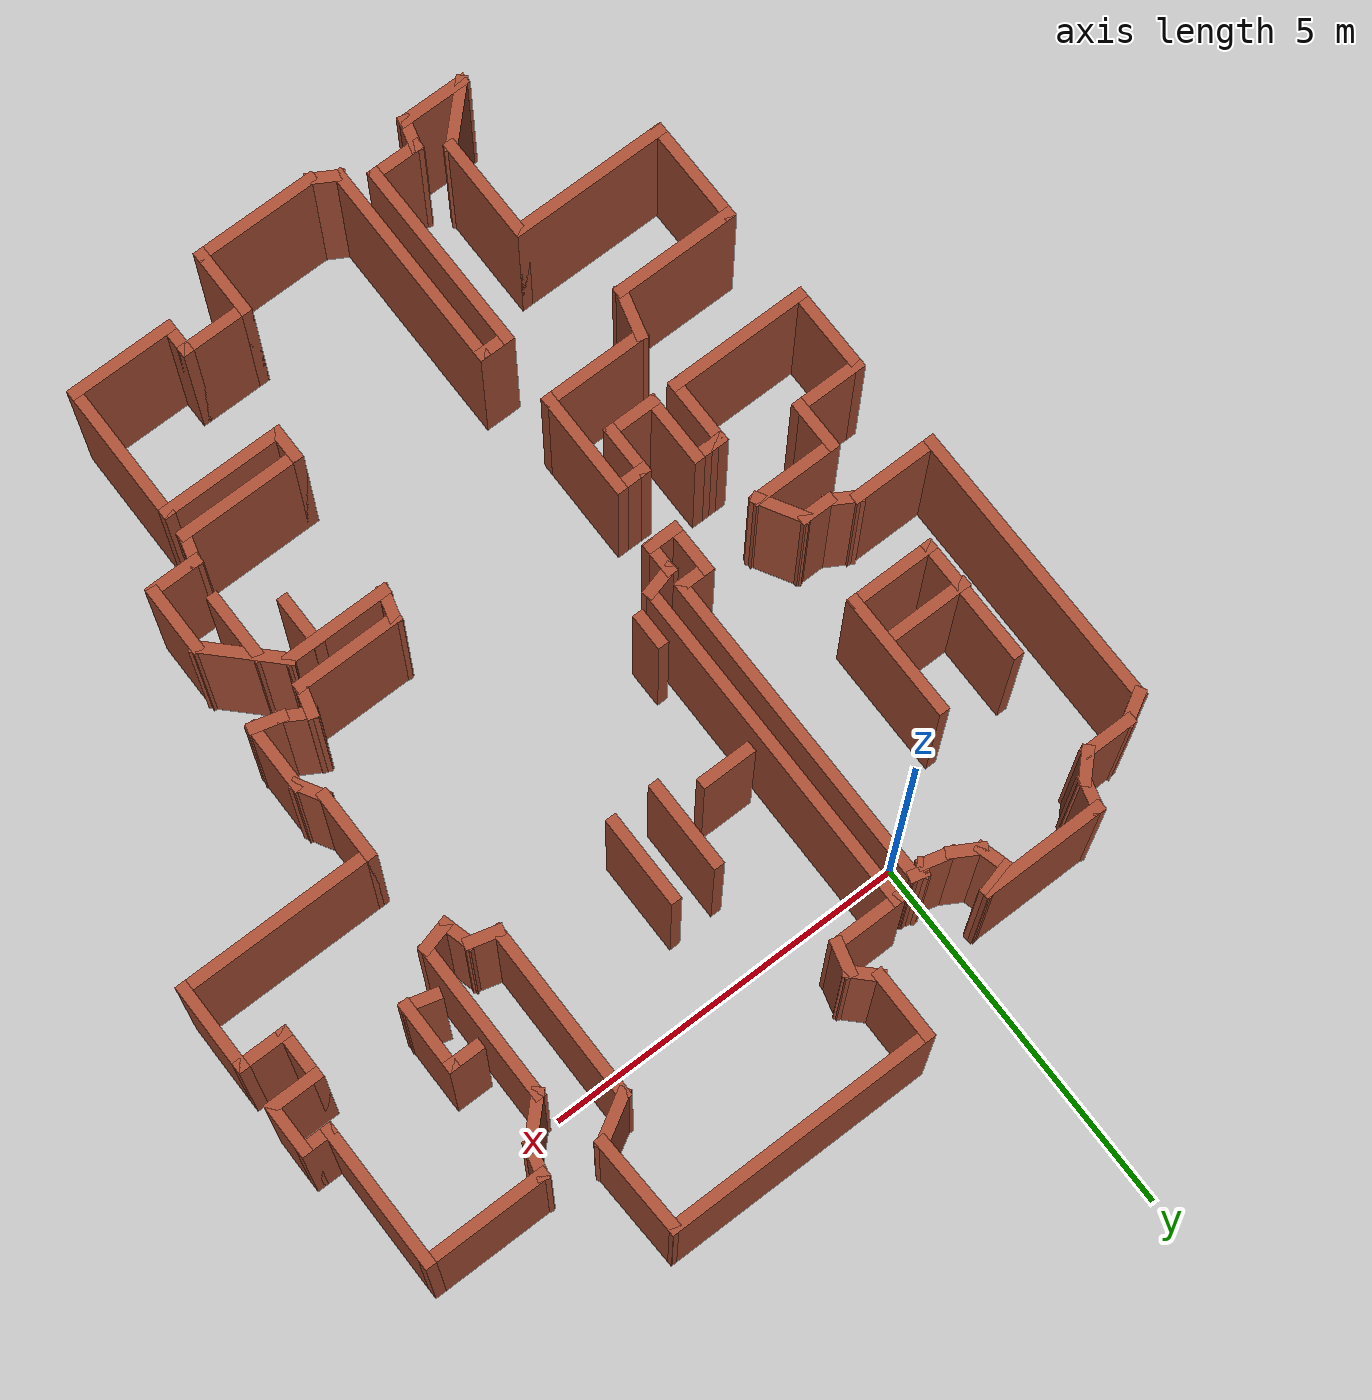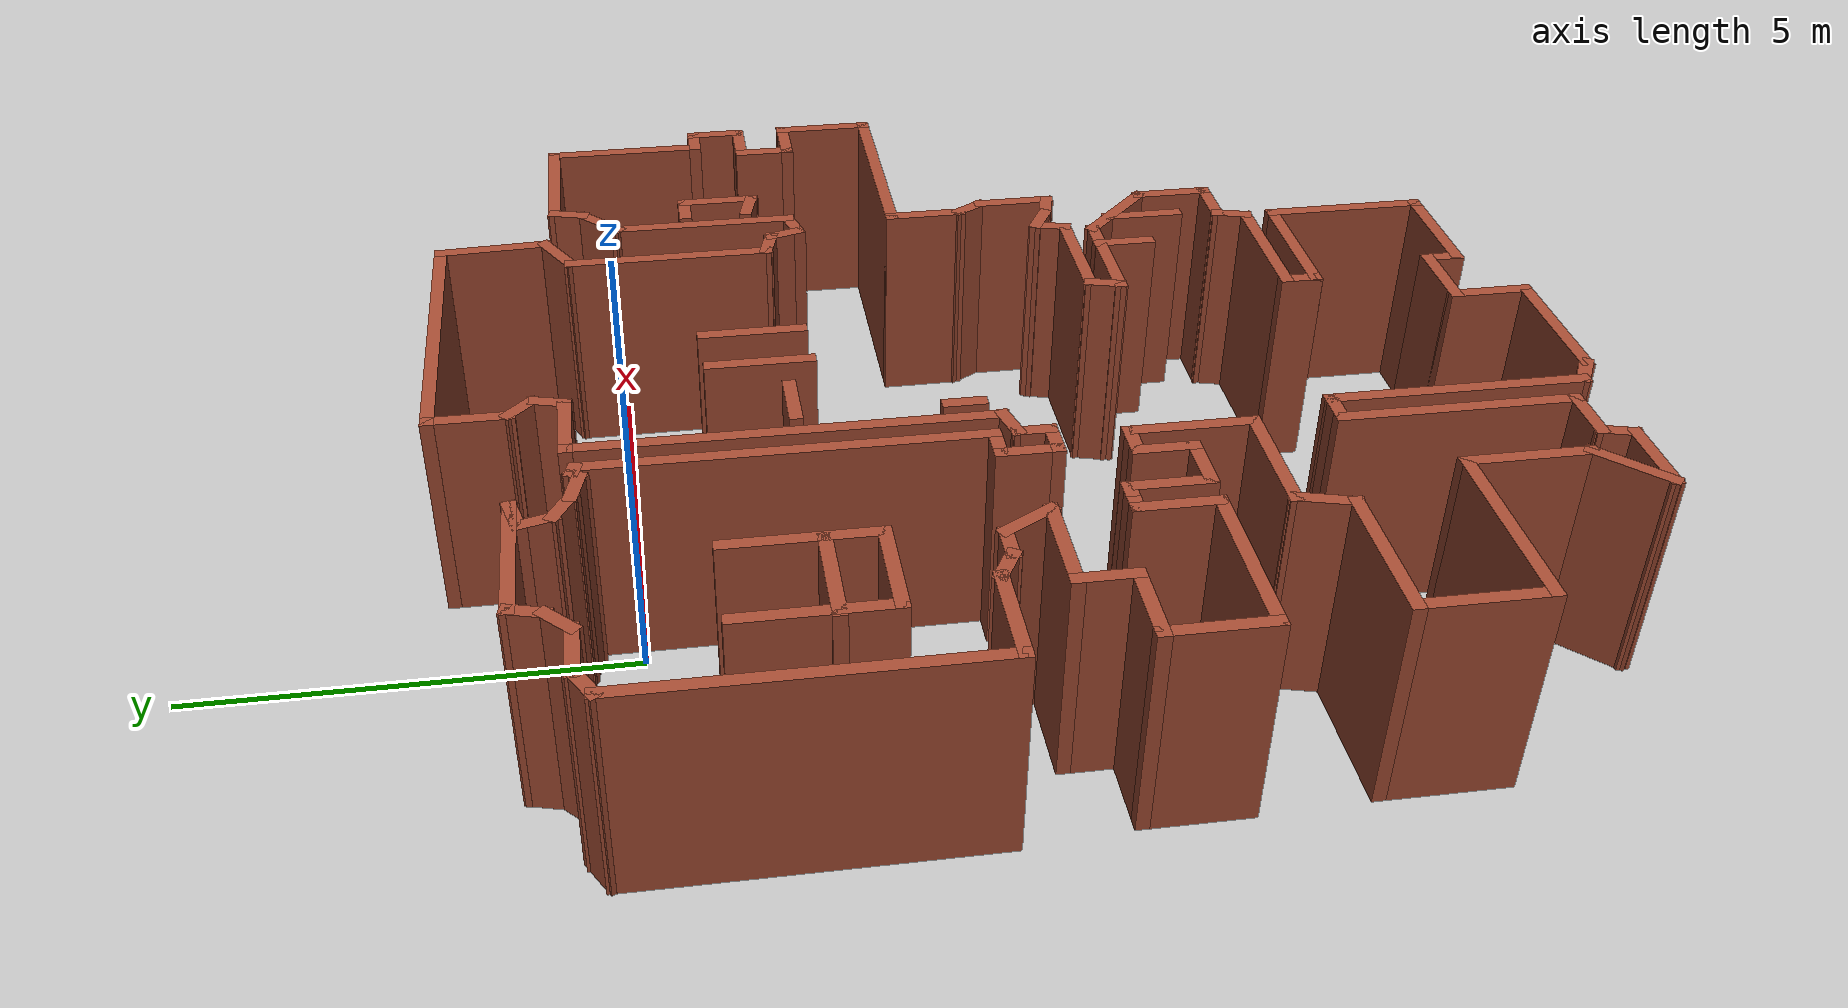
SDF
<?xml version='1.0'?>
<sdf version='1.6'>
  <model name='map_17'>
    <pose frame=''>2.25435 -4.22209 0 0 -0 0</pose>
    <link name='Wall_0'>
      <collision name='Wall_0_Collision'>
        <geometry>
          <box>
            <size>3.75 0.15 2.5</size>
          </box>
        </geometry>
        <pose frame=''>0 0 1.25 0 -0 0</pose>
      </collision>
      <visual name='Wall_0_Visual'>
        <pose frame=''>0 0 1.25 0 -0 0</pose>
        <geometry>
          <box>
            <size>3.75 0.15 2.5</size>
          </box>
        </geometry>
        <material>
          <script>
            <uri>file://media/materials/scripts/gazebo.material</uri>
            <name>Gazebo/Bricks</name>
          </script>
          <ambient>1 1 1 1</ambient>
        </material>
        <meta>
          <layer>0</layer>
        </meta>
      </visual>
      <pose frame=''>0.846782 6.31181 0 0 -0 3.14159</pose>
    </link>
    <link name='Wall_1'>
      <collision name='Wall_1_Collision'>
        <geometry>
          <box>
            <size>1 0.15 2.5</size>
          </box>
        </geometry>
        <pose frame=''>0 0 1.25 0 -0 0</pose>
      </collision>
      <visual name='Wall_1_Visual'>
        <pose frame=''>0 0 1.25 0 -0 0</pose>
        <geometry>
          <box>
            <size>1 0.15 2.5</size>
          </box>
        </geometry>
        <material>
          <script>
            <uri>file://media/materials/scripts/gazebo.material</uri>
            <name>Gazebo/Bricks</name>
          </script>
          <ambient>1 1 1 1</ambient>
        </material>
        <meta>
          <layer>0</layer>
        </meta>
      </visual>
      <pose frame=''>-0.953218 5.88681 0 0 -0 -1.5708</pose>
    </link>
    <link name='Wall_10'>
      <collision name='Wall_10_Collision'>
        <geometry>
          <box>
            <size>0.5 0.15 2.5</size>
          </box>
        </geometry>
        <pose frame=''>0 0 1.25 0 -0 0</pose>
      </collision>
      <visual name='Wall_10_Visual'>
        <pose frame=''>0 0 1.25 0 -0 0</pose>
        <geometry>
          <box>
            <size>0.5 0.15 2.5</size>
          </box>
        </geometry>
        <material>
          <script>
            <uri>file://media/materials/scripts/gazebo.material</uri>
            <name>Gazebo/Bricks</name>
          </script>
          <ambient>1 1 1 1</ambient>
        </material>
        <meta>
          <layer>0</layer>
        </meta>
      </visual>
      <pose frame=''>-2.15939 0.435665 0 0 -0 0</pose>
    </link>
    <link name='Wall_100'>
      <collision name='Wall_100_Collision'>
        <geometry>
          <box>
            <size>0.5 0.15 2.5</size>
          </box>
        </geometry>
        <pose frame=''>0 0 1.25 0 -0 0</pose>
      </collision>
      <visual name='Wall_100_Visual'>
        <pose frame=''>0 0 1.25 0 -0 0</pose>
        <geometry>
          <box>
            <size>0.5 0.15 2.5</size>
          </box>
        </geometry>
        <material>
          <script>
            <uri>file://media/materials/scripts/gazebo.material</uri>
            <name>Gazebo/Bricks</name>
          </script>
          <ambient>1 1 1 1</ambient>
        </material>
        <meta>
          <layer>0</layer>
        </meta>
      </visual>
      <pose frame=''>2.56581 2.15806 0 0 -0 1.8326</pose>
    </link>
    <link name='Wall_101'>
      <collision name='Wall_101_Collision'>
        <geometry>
          <box>
            <size>0.5 0.15 2.5</size>
          </box>
        </geometry>
        <pose frame=''>0 0 1.25 0 -0 0</pose>
      </collision>
      <visual name='Wall_101_Visual'>
        <pose frame=''>0 0 1.25 0 -0 0</pose>
        <geometry>
          <box>
            <size>0.5 0.15 2.5</size>
          </box>
        </geometry>
        <material>
          <script>
            <uri>file://media/materials/scripts/gazebo.material</uri>
            <name>Gazebo/Bricks</name>
          </script>
          <ambient>1 1 1 1</ambient>
        </material>
        <meta>
          <layer>0</layer>
        </meta>
      </visual>
      <pose frame=''>2.35148 2.37239 0 0 -0 2.87979</pose>
    </link>
    <link name='Wall_102'>
      <collision name='Wall_102_Collision'>
        <geometry>
          <box>
            <size>2.5 0.15 2.5</size>
          </box>
        </geometry>
        <pose frame=''>0 0 1.25 0 -0 0</pose>
      </collision>
      <visual name='Wall_102_Visual'>
        <pose frame=''>0 0 1.25 0 -0 0</pose>
        <geometry>
          <box>
            <size>2.5 0.15 2.5</size>
          </box>
        </geometry>
        <material>
          <script>
            <uri>file://media/materials/scripts/gazebo.material</uri>
            <name>Gazebo/Bricks</name>
          </script>
          <ambient>1 1 1 1</ambient>
        </material>
        <meta>
          <layer>0</layer>
        </meta>
      </visual>
      <pose frame=''>2.18244 3.59268 0 0 -0 1.5708</pose>
    </link>
    <link name='Wall_103'>
      <collision name='Wall_103_Collision'>
        <geometry>
          <box>
            <size>0.75 0.15 2.5</size>
          </box>
        </geometry>
        <pose frame=''>0 0 1.25 0 -0 0</pose>
      </collision>
      <visual name='Wall_103_Visual'>
        <pose frame=''>0 0 1.25 0 -0 0</pose>
        <geometry>
          <box>
            <size>0.75 0.15 2.5</size>
          </box>
        </geometry>
        <material>
          <script>
            <uri>file://media/materials/scripts/gazebo.material</uri>
            <name>Gazebo/Bricks</name>
          </script>
          <ambient>1 1 1 1</ambient>
        </material>
        <meta>
          <layer>0</layer>
        </meta>
      </visual>
      <pose frame=''>2.44225 4.91768 0 0 -0 0.523599</pose>
    </link>
    <link name='Wall_104'>
      <collision name='Wall_104_Collision'>
        <geometry>
          <box>
            <size>1.39536 0.15 2.5</size>
          </box>
        </geometry>
        <pose frame=''>0 0 1.25 0 -0 0</pose>
      </collision>
      <visual name='Wall_104_Visual'>
        <pose frame=''>0 0 1.25 0 -0 0</pose>
        <geometry>
          <box>
            <size>1.39536 0.15 2.5</size>
          </box>
        </geometry>
        <material>
          <script>
            <uri>file://media/materials/scripts/gazebo.material</uri>
            <name>Gazebo/Bricks</name>
          </script>
          <ambient>1 1 1 1</ambient>
        </material>
        <meta>
          <layer>0</layer>
        </meta>
      </visual>
      <pose frame=''>2.67442 5.68975 0 0 -0 1.61519</pose>
    </link>
    <link name='Wall_106'>
      <collision name='Wall_106_Collision'>
        <geometry>
          <box>
            <size>1.75 0.15 2.5</size>
          </box>
        </geometry>
        <pose frame=''>0 0 1.25 0 -0 0</pose>
      </collision>
      <visual name='Wall_106_Visual'>
        <pose frame=''>0 0 1.25 0 -0 0</pose>
        <geometry>
          <box>
            <size>1.75 0.15 2.5</size>
          </box>
        </geometry>
        <material>
          <script>
            <uri>file://media/materials/scripts/gazebo.material</uri>
            <name>Gazebo/Bricks</name>
          </script>
          <ambient>1 1 1 1</ambient>
        </material>
        <meta>
          <layer>0</layer>
        </meta>
      </visual>
      <pose frame=''>-4.56187 2.61239 0 0 -0 -1.5708</pose>
    </link>
    <link name='Wall_107'>
      <collision name='Wall_107_Collision'>
        <geometry>
          <box>
            <size>1.25 0.15 2.5</size>
          </box>
        </geometry>
        <pose frame=''>0 0 1.25 0 -0 0</pose>
      </collision>
      <visual name='Wall_107_Visual'>
        <pose frame=''>0 0 1.25 0 -0 0</pose>
        <geometry>
          <box>
            <size>1.25 0.15 2.5</size>
          </box>
        </geometry>
        <material>
          <script>
            <uri>file://media/materials/scripts/gazebo.material</uri>
            <name>Gazebo/Bricks</name>
          </script>
          <ambient>1 1 1 1</ambient>
        </material>
        <meta>
          <layer>0</layer>
        </meta>
      </visual>
      <pose frame=''>-4.01187 1.81239 0 0 -0 0</pose>
    </link>
    <link name='Wall_108'>
      <collision name='Wall_108_Collision'>
        <geometry>
          <box>
            <size>1.75 0.15 2.5</size>
          </box>
        </geometry>
        <pose frame=''>0 0 1.25 0 -0 0</pose>
      </collision>
      <visual name='Wall_108_Visual'>
        <pose frame=''>0 0 1.25 0 -0 0</pose>
        <geometry>
          <box>
            <size>1.75 0.15 2.5</size>
          </box>
        </geometry>
        <material>
          <script>
            <uri>file://media/materials/scripts/gazebo.material</uri>
            <name>Gazebo/Bricks</name>
          </script>
          <ambient>1 1 1 1</ambient>
        </material>
        <meta>
          <layer>0</layer>
        </meta>
      </visual>
      <pose frame=''>-3.46187 2.61239 0 0 -0 1.5708</pose>
    </link>
    <link name='Wall_11'>
      <collision name='Wall_11_Collision'>
        <geometry>
          <box>
            <size>4.5 0.15 2.5</size>
          </box>
        </geometry>
        <pose frame=''>0 0 1.25 0 -0 0</pose>
      </collision>
      <visual name='Wall_11_Visual'>
        <pose frame=''>0 0 1.25 0 -0 0</pose>
        <geometry>
          <box>
            <size>4.5 0.15 2.5</size>
          </box>
        </geometry>
        <material>
          <script>
            <uri>file://media/materials/scripts/gazebo.material</uri>
            <name>Gazebo/Bricks</name>
          </script>
          <ambient>1 1 1 1</ambient>
        </material>
        <meta>
          <layer>0</layer>
        </meta>
      </visual>
      <pose frame=''>-1.98439 2.61066 0 0 -0 1.5708</pose>
    </link>
    <link name='Wall_110'>
      <collision name='Wall_110_Collision'>
        <geometry>
          <box>
            <size>1.25 0.15 2.5</size>
          </box>
        </geometry>
        <pose frame=''>0 0 1.25 0 -0 0</pose>
      </collision>
      <visual name='Wall_110_Visual'>
        <pose frame=''>0 0 1.25 0 -0 0</pose>
        <geometry>
          <box>
            <size>1.25 0.15 2.5</size>
          </box>
        </geometry>
        <material>
          <script>
            <uri>file://media/materials/scripts/gazebo.material</uri>
            <name>Gazebo/Bricks</name>
          </script>
          <ambient>1 1 1 1</ambient>
        </material>
        <meta>
          <layer>0</layer>
        </meta>
      </visual>
      <pose frame=''>-4.03847 2.40158 0 0 -0 0</pose>
    </link>
    <link name='Wall_112'>
      <collision name='Wall_112_Collision'>
        <geometry>
          <box>
            <size>1.25 0.15 2.5</size>
          </box>
        </geometry>
        <pose frame=''>0 0 1.25 0 -0 0</pose>
      </collision>
      <visual name='Wall_112_Visual'>
        <pose frame=''>0 0 1.25 0 -0 0</pose>
        <geometry>
          <box>
            <size>1.25 0.15 2.5</size>
          </box>
        </geometry>
        <material>
          <script>
            <uri>file://media/materials/scripts/gazebo.material</uri>
            <name>Gazebo/Bricks</name>
          </script>
          <ambient>1 1 1 1</ambient>
        </material>
        <meta>
          <layer>0</layer>
        </meta>
      </visual>
      <pose frame=''>-0.27924 2.72939 0 0 -0 -1.5708</pose>
    </link>
    <link name='Wall_114'>
      <collision name='Wall_114_Collision'>
        <geometry>
          <box>
            <size>1.25 0.15 2.5</size>
          </box>
        </geometry>
        <pose frame=''>0 0 1.25 0 -0 0</pose>
      </collision>
      <visual name='Wall_114_Visual'>
        <pose frame=''>0 0 1.25 0 -0 0</pose>
        <geometry>
          <box>
            <size>1.25 0.15 2.5</size>
          </box>
        </geometry>
        <material>
          <script>
            <uri>file://media/materials/scripts/gazebo.material</uri>
            <name>Gazebo/Bricks</name>
          </script>
          <ambient>1 1 1 1</ambient>
        </material>
        <meta>
          <layer>0</layer>
        </meta>
      </visual>
      <pose frame=''>0.359165 2.75599 0 0 -0 -1.5708</pose>
    </link>
    <link name='Wall_116'>
      <collision name='Wall_116_Collision'>
        <geometry>
          <box>
            <size>0.75 0.15 2.5</size>
          </box>
        </geometry>
        <pose frame=''>0 0 1.25 0 -0 0</pose>
      </collision>
      <visual name='Wall_116_Visual'>
        <pose frame=''>0 0 1.25 0 -0 0</pose>
        <geometry>
          <box>
            <size>0.75 0.15 2.5</size>
          </box>
        </geometry>
        <material>
          <script>
            <uri>file://media/materials/scripts/gazebo.material</uri>
            <name>Gazebo/Bricks</name>
          </script>
          <ambient>1 1 1 1</ambient>
        </material>
        <meta>
          <layer>0</layer>
        </meta>
      </visual>
      <pose frame=''>-1.06985 2.45478 0 0 -0 0</pose>
    </link>
    <link name='Wall_118'>
      <collision name='Wall_118_Collision'>
        <geometry>
          <box>
            <size>0.5 0.15 2.5</size>
          </box>
        </geometry>
        <pose frame=''>0 0 1.25 0 -0 0</pose>
      </collision>
      <visual name='Wall_118_Visual'>
        <pose frame=''>0 0 1.25 0 -0 0</pose>
        <geometry>
          <box>
            <size>0.5 0.15 2.5</size>
          </box>
        </geometry>
        <material>
          <script>
            <uri>file://media/materials/scripts/gazebo.material</uri>
            <name>Gazebo/Bricks</name>
          </script>
          <ambient>1 1 1 1</ambient>
        </material>
        <meta>
          <layer>0</layer>
        </meta>
      </visual>
      <pose frame=''>3.35379 3.33259 0 0 -0 0</pose>
    </link>
    <link name='Wall_119'>
      <collision name='Wall_119_Collision'>
        <geometry>
          <box>
            <size>1 0.15 2.5</size>
          </box>
        </geometry>
        <pose frame=''>0 0 1.25 0 -0 0</pose>
      </collision>
      <visual name='Wall_119_Visual'>
        <pose frame=''>0 0 1.25 0 -0 0</pose>
        <geometry>
          <box>
            <size>1 0.15 2.5</size>
          </box>
        </geometry>
        <material>
          <script>
            <uri>file://media/materials/scripts/gazebo.material</uri>
            <name>Gazebo/Bricks</name>
          </script>
          <ambient>1 1 1 1</ambient>
        </material>
        <meta>
          <layer>0</layer>
        </meta>
      </visual>
      <pose frame=''>3.52879 2.90759 0 0 -0 -1.5708</pose>
    </link>
    <link name='Wall_12'>
      <collision name='Wall_12_Collision'>
        <geometry>
          <box>
            <size>0.25 0.15 2.5</size>
          </box>
        </geometry>
        <pose frame=''>0 0 1.25 0 -0 0</pose>
      </collision>
      <visual name='Wall_12_Visual'>
        <pose frame=''>0 0 1.25 0 -0 0</pose>
        <geometry>
          <box>
            <size>0.25 0.15 2.5</size>
          </box>
        </geometry>
        <material>
          <script>
            <uri>file://media/materials/scripts/gazebo.material</uri>
            <name>Gazebo/Bricks</name>
          </script>
          <ambient>1 1 1 1</ambient>
        </material>
        <meta>
          <layer>0</layer>
        </meta>
      </visual>
      <pose frame=''>-2.03269 4.79861 0 0 -0 2.87979</pose>
    </link>
    <link name='Wall_120'>
      <collision name='Wall_120_Collision'>
        <geometry>
          <box>
            <size>0.5 0.15 2.5</size>
          </box>
        </geometry>
        <pose frame=''>0 0 1.25 0 -0 0</pose>
      </collision>
      <visual name='Wall_120_Visual'>
        <pose frame=''>0 0 1.25 0 -0 0</pose>
        <geometry>
          <box>
            <size>0.5 0.15 2.5</size>
          </box>
        </geometry>
        <material>
          <script>
            <uri>file://media/materials/scripts/gazebo.material</uri>
            <name>Gazebo/Bricks</name>
          </script>
          <ambient>1 1 1 1</ambient>
        </material>
        <meta>
          <layer>0</layer>
        </meta>
      </visual>
      <pose frame=''>3.35975 2.52788 0 0 -0 2.87979</pose>
    </link>
    <link name='Wall_122'>
      <collision name='Wall_122_Collision'>
        <geometry>
          <box>
            <size>0.75 0.15 2.5</size>
          </box>
        </geometry>
        <pose frame=''>0 0 1.25 0 -0 0</pose>
      </collision>
      <visual name='Wall_122_Visual'>
        <pose frame=''>0 0 1.25 0 -0 0</pose>
        <geometry>
          <box>
            <size>0.75 0.15 2.5</size>
          </box>
        </geometry>
        <material>
          <script>
            <uri>file://media/materials/scripts/gazebo.material</uri>
            <name>Gazebo/Bricks</name>
          </script>
          <ambient>1 1 1 1</ambient>
        </material>
        <meta>
          <layer>0</layer>
        </meta>
      </visual>
      <pose frame=''>1.79557 -1.91505 0 0 -0 -1.5708</pose>
    </link>
    <link name='Wall_124'>
      <collision name='Wall_124_Collision'>
        <geometry>
          <box>
            <size>1 0.15 2.5</size>
          </box>
        </geometry>
        <pose frame=''>0 0 1.25 0 -0 0</pose>
      </collision>
      <visual name='Wall_124_Visual'>
        <pose frame=''>0 0 1.25 0 -0 0</pose>
        <geometry>
          <box>
            <size>1 0.15 2.5</size>
          </box>
        </geometry>
        <material>
          <script>
            <uri>file://media/materials/scripts/gazebo.material</uri>
            <name>Gazebo/Bricks</name>
          </script>
          <ambient>1 1 1 1</ambient>
        </material>
        <meta>
          <layer>0</layer>
        </meta>
      </visual>
      <pose frame=''>2.43398 -2.30605 0 0 -0 -1.5708</pose>
    </link>
    <link name='Wall_126'>
      <collision name='Wall_126_Collision'>
        <geometry>
          <box>
            <size>0.5 0.15 2.5</size>
          </box>
        </geometry>
        <pose frame=''>0 0 1.25 0 -0 0</pose>
      </collision>
      <visual name='Wall_126_Visual'>
        <pose frame=''>0 0 1.25 0 -0 0</pose>
        <geometry>
          <box>
            <size>0.5 0.15 2.5</size>
          </box>
        </geometry>
        <material>
          <script>
            <uri>file://media/materials/scripts/gazebo.material</uri>
            <name>Gazebo/Bricks</name>
          </script>
          <ambient>1 1 1 1</ambient>
        </material>
        <meta>
          <layer>0</layer>
        </meta>
      </visual>
      <pose frame=''>-1.36985 0.634769 0 0 -0 1.5708</pose>
    </link>
    <link name='Wall_13'>
      <collision name='Wall_13_Collision'>
        <geometry>
          <box>
            <size>0.25 0.15 2.5</size>
          </box>
        </geometry>
        <pose frame=''>0 0 1.25 0 -0 0</pose>
      </collision>
      <visual name='Wall_13_Visual'>
        <pose frame=''>0 0 1.25 0 -0 0</pose>
        <geometry>
          <box>
            <size>0.25 0.15 2.5</size>
          </box>
        </geometry>
        <material>
          <script>
            <uri>file://media/materials/scripts/gazebo.material</uri>
            <name>Gazebo/Bricks</name>
          </script>
          <ambient>1 1 1 1</ambient>
        </material>
        <meta>
          <layer>0</layer>
        </meta>
      </visual>
      <pose frame=''>-2.11634 4.77619 0 0 -0 -2.35619</pose>
    </link>
    <link name='Wall_14'>
      <collision name='Wall_14_Collision'>
        <geometry>
          <box>
            <size>0.5 0.15 2.5</size>
          </box>
        </geometry>
        <pose frame=''>0 0 1.25 0 -0 0</pose>
      </collision>
      <visual name='Wall_14_Visual'>
        <pose frame=''>0 0 1.25 0 -0 0</pose>
        <geometry>
          <box>
            <size>0.5 0.15 2.5</size>
          </box>
        </geometry>
        <material>
          <script>
            <uri>file://media/materials/scripts/gazebo.material</uri>
            <name>Gazebo/Bricks</name>
          </script>
          <ambient>1 1 1 1</ambient>
        </material>
        <meta>
          <layer>0</layer>
        </meta>
      </visual>
      <pose frame=''>-2.32073 4.78613 0 0 -0 2.87979</pose>
    </link>
    <link name='Wall_15'>
      <collision name='Wall_15_Collision'>
        <geometry>
          <box>
            <size>0.5 0.15 2.5</size>
          </box>
        </geometry>
        <pose frame=''>0 0 1.25 0 -0 0</pose>
      </collision>
      <visual name='Wall_15_Visual'>
        <pose frame=''>0 0 1.25 0 -0 0</pose>
        <geometry>
          <box>
            <size>0.5 0.15 2.5</size>
          </box>
        </geometry>
        <material>
          <script>
            <uri>file://media/materials/scripts/gazebo.material</uri>
            <name>Gazebo/Bricks</name>
          </script>
          <ambient>1 1 1 1</ambient>
        </material>
        <meta>
          <layer>0</layer>
        </meta>
      </visual>
      <pose frame=''>-2.64132 4.91892 0 0 -0 2.61799</pose>
    </link>
    <link name='Wall_16'>
      <collision name='Wall_16_Collision'>
        <geometry>
          <box>
            <size>0.5 0.15 2.5</size>
          </box>
        </geometry>
        <pose frame=''>0 0 1.25 0 -0 0</pose>
      </collision>
      <visual name='Wall_16_Visual'>
        <pose frame=''>0 0 1.25 0 -0 0</pose>
        <geometry>
          <box>
            <size>0.5 0.15 2.5</size>
          </box>
        </geometry>
        <material>
          <script>
            <uri>file://media/materials/scripts/gazebo.material</uri>
            <name>Gazebo/Bricks</name>
          </script>
          <ambient>1 1 1 1</ambient>
        </material>
        <meta>
          <layer>0</layer>
        </meta>
      </visual>
      <pose frame=''>-2.83817 5.17546 0 0 -0 1.8326</pose>
    </link>
    <link name='Wall_17'>
      <collision name='Wall_17_Collision'>
        <geometry>
          <box>
            <size>0.5 0.15 2.5</size>
          </box>
        </geometry>
        <pose frame=''>0 0 1.25 0 -0 0</pose>
      </collision>
      <visual name='Wall_17_Visual'>
        <pose frame=''>0 0 1.25 0 -0 0</pose>
        <geometry>
          <box>
            <size>0.5 0.15 2.5</size>
          </box>
        </geometry>
        <material>
          <script>
            <uri>file://media/materials/scripts/gazebo.material</uri>
            <name>Gazebo/Bricks</name>
          </script>
          <ambient>1 1 1 1</ambient>
        </material>
        <meta>
          <layer>0</layer>
        </meta>
      </visual>
      <pose frame=''>-2.71443 5.38979 0 0 -0 0.261799</pose>
    </link>
    <link name='Wall_18'>
      <collision name='Wall_18_Collision'>
        <geometry>
          <box>
            <size>1.75 0.15 2.5</size>
          </box>
        </geometry>
        <pose frame=''>0 0 1.25 0 -0 0</pose>
      </collision>
      <visual name='Wall_18_Visual'>
        <pose frame=''>0 0 1.25 0 -0 0</pose>
        <geometry>
          <box>
            <size>1.75 0.15 2.5</size>
          </box>
        </geometry>
        <material>
          <script>
            <uri>file://media/materials/scripts/gazebo.material</uri>
            <name>Gazebo/Bricks</name>
          </script>
          <ambient>1 1 1 1</ambient>
        </material>
        <meta>
          <layer>0</layer>
        </meta>
      </visual>
      <pose frame=''>-3.34539 5.43508 0 0 -0 3.14159</pose>
    </link>
    <link name='Wall_19'>
      <collision name='Wall_19_Collision'>
        <geometry>
          <box>
            <size>0.5 0.15 2.5</size>
          </box>
        </geometry>
        <pose frame=''>0 0 1.25 0 -0 0</pose>
      </collision>
      <visual name='Wall_19_Visual'>
        <pose frame=''>0 0 1.25 0 -0 0</pose>
        <geometry>
          <box>
            <size>0.5 0.15 2.5</size>
          </box>
        </geometry>
        <material>
          <script>
            <uri>file://media/materials/scripts/gazebo.material</uri>
            <name>Gazebo/Bricks</name>
          </script>
          <ambient>1 1 1 1</ambient>
        </material>
        <meta>
          <layer>0</layer>
        </meta>
      </visual>
      <pose frame=''>-4.19068 5.26605 0 0 -0 -1.8326</pose>
    </link>
    <link name='Wall_2'>
      <collision name='Wall_2_Collision'>
        <geometry>
          <box>
            <size>0.5 0.15 2.5</size>
          </box>
        </geometry>
        <pose frame=''>0 0 1.25 0 -0 0</pose>
      </collision>
      <visual name='Wall_2_Visual'>
        <pose frame=''>0 0 1.25 0 -0 0</pose>
        <geometry>
          <box>
            <size>0.5 0.15 2.5</size>
          </box>
        </geometry>
        <material>
          <script>
            <uri>file://media/materials/scripts/gazebo.material</uri>
            <name>Gazebo/Bricks</name>
          </script>
          <ambient>1 1 1 1</ambient>
        </material>
        <meta>
          <layer>0</layer>
        </meta>
      </visual>
      <pose frame=''>-0.829474 5.33807 0 0 -0 -0.785398</pose>
    </link>
    <link name='Wall_20'>
      <collision name='Wall_20_Collision'>
        <geometry>
          <box>
            <size>0.5 0.15 2.5</size>
          </box>
        </geometry>
        <pose frame=''>0 0 1.25 0 -0 0</pose>
      </collision>
      <visual name='Wall_20_Visual'>
        <pose frame=''>0 0 1.25 0 -0 0</pose>
        <geometry>
          <box>
            <size>0.5 0.15 2.5</size>
          </box>
        </geometry>
        <material>
          <script>
            <uri>file://media/materials/scripts/gazebo.material</uri>
            <name>Gazebo/Bricks</name>
          </script>
          <ambient>1 1 1 1</ambient>
        </material>
        <meta>
          <layer>0</layer>
        </meta>
      </visual>
      <pose frame=''>-4.35972 4.97326 0 0 -0 -2.35619</pose>
    </link>
    <link name='Wall_21'>
      <collision name='Wall_21_Collision'>
        <geometry>
          <box>
            <size>0.75 0.15 2.5</size>
          </box>
        </geometry>
        <pose frame=''>0 0 1.25 0 -0 0</pose>
      </collision>
      <visual name='Wall_21_Visual'>
        <pose frame=''>0 0 1.25 0 -0 0</pose>
        <geometry>
          <box>
            <size>0.75 0.15 2.5</size>
          </box>
        </geometry>
        <material>
          <script>
            <uri>file://media/materials/scripts/gazebo.material</uri>
            <name>Gazebo/Bricks</name>
          </script>
          <ambient>1 1 1 1</ambient>
        </material>
        <meta>
          <layer>0</layer>
        </meta>
      </visual>
      <pose frame=''>-4.78346 4.84952 0 0 -0 3.14159</pose>
    </link>
    <link name='Wall_22'>
      <collision name='Wall_22_Collision'>
        <geometry>
          <box>
            <size>0.5 0.15 2.5</size>
          </box>
        </geometry>
        <pose frame=''>0 0 1.25 0 -0 0</pose>
      </collision>
      <visual name='Wall_22_Visual'>
        <pose frame=''>0 0 1.25 0 -0 0</pose>
        <geometry>
          <box>
            <size>0.5 0.15 2.5</size>
          </box>
        </geometry>
        <material>
          <script>
            <uri>file://media/materials/scripts/gazebo.material</uri>
            <name>Gazebo/Bricks</name>
          </script>
          <ambient>1 1 1 1</ambient>
        </material>
        <meta>
          <layer>0</layer>
        </meta>
      </visual>
      <pose frame=''>-5.23502 4.76202 0 0 -0 -2.61799</pose>
    </link>
    <link name='Wall_23'>
      <collision name='Wall_23_Collision'>
        <geometry>
          <box>
            <size>4 0.15 2.5</size>
          </box>
        </geometry>
        <pose frame=''>0 0 1.25 0 -0 0</pose>
      </collision>
      <visual name='Wall_23_Visual'>
        <pose frame=''>0 0 1.25 0 -0 0</pose>
        <geometry>
          <box>
            <size>4 0.15 2.5</size>
          </box>
        </geometry>
        <material>
          <script>
            <uri>file://media/materials/scripts/gazebo.material</uri>
            <name>Gazebo/Bricks</name>
          </script>
          <ambient>1 1 1 1</ambient>
        </material>
        <meta>
          <layer>0</layer>
        </meta>
      </visual>
      <pose frame=''>-5.38657 2.74952 0 0 -0 -1.5708</pose>
    </link>
    <link name='Wall_24'>
      <collision name='Wall_24_Collision'>
        <geometry>
          <box>
            <size>1.25 0.15 2.5</size>
          </box>
        </geometry>
        <pose frame=''>0 0 1.25 0 -0 0</pose>
      </collision>
      <visual name='Wall_24_Visual'>
        <pose frame=''>0 0 1.25 0 -0 0</pose>
        <geometry>
          <box>
            <size>1.25 0.15 2.5</size>
          </box>
        </geometry>
        <material>
          <script>
            <uri>file://media/materials/scripts/gazebo.material</uri>
            <name>Gazebo/Bricks</name>
          </script>
          <ambient>1 1 1 1</ambient>
        </material>
        <meta>
          <layer>0</layer>
        </meta>
      </visual>
      <pose frame=''>-4.83657 0.824522 0 0 -0 0</pose>
    </link>
    <link name='Wall_25'>
      <collision name='Wall_25_Collision'>
        <geometry>
          <box>
            <size>0.5 0.15 2.5</size>
          </box>
        </geometry>
        <pose frame=''>0 0 1.25 0 -0 0</pose>
      </collision>
      <visual name='Wall_25_Visual'>
        <pose frame=''>0 0 1.25 0 -0 0</pose>
        <geometry>
          <box>
            <size>0.5 0.15 2.5</size>
          </box>
        </geometry>
        <material>
          <script>
            <uri>file://media/materials/scripts/gazebo.material</uri>
            <name>Gazebo/Bricks</name>
          </script>
          <ambient>1 1 1 1</ambient>
        </material>
        <meta>
          <layer>0</layer>
        </meta>
      </visual>
      <pose frame=''>-4.13502 0.737022 0 0 -0 -0.523599</pose>
    </link>
    <link name='Wall_26'>
      <collision name='Wall_26_Collision'>
        <geometry>
          <box>
            <size>0.5 0.15 2.5</size>
          </box>
        </geometry>
        <pose frame=''>0 0 1.25 0 -0 0</pose>
      </collision>
      <visual name='Wall_26_Visual'>
        <pose frame=''>0 0 1.25 0 -0 0</pose>
        <geometry>
          <box>
            <size>0.5 0.15 2.5</size>
          </box>
        </geometry>
        <material>
          <script>
            <uri>file://media/materials/scripts/gazebo.material</uri>
            <name>Gazebo/Bricks</name>
          </script>
          <ambient>1 1 1 1</ambient>
        </material>
        <meta>
          <layer>0</layer>
        </meta>
      </visual>
      <pose frame=''>-3.80846 0.649522 0 0 -0 0</pose>
    </link>
    <link name='Wall_27'>
      <collision name='Wall_27_Collision'>
        <geometry>
          <box>
            <size>0.75 0.15 2.5</size>
          </box>
        </geometry>
        <pose frame=''>0 0 1.25 0 -0 0</pose>
      </collision>
      <visual name='Wall_27_Visual'>
        <pose frame=''>0 0 1.25 0 -0 0</pose>
        <geometry>
          <box>
            <size>0.75 0.15 2.5</size>
          </box>
        </geometry>
        <material>
          <script>
            <uri>file://media/materials/scripts/gazebo.material</uri>
            <name>Gazebo/Bricks</name>
          </script>
          <ambient>1 1 1 1</ambient>
        </material>
        <meta>
          <layer>0</layer>
        </meta>
      </visual>
      <pose frame=''>-3.48346 0.389714 0 0 -0 -1.0472</pose>
    </link>
    <link name='Wall_28'>
      <collision name='Wall_28_Collision'>
        <geometry>
          <box>
            <size>1.25 0.15 2.5</size>
          </box>
        </geometry>
        <pose frame=''>0 0 1.25 0 -0 0</pose>
      </collision>
      <visual name='Wall_28_Visual'>
        <pose frame=''>0 0 1.25 0 -0 0</pose>
        <geometry>
          <box>
            <size>1.25 0.15 2.5</size>
          </box>
        </geometry>
        <material>
          <script>
            <uri>file://media/materials/scripts/gazebo.material</uri>
            <name>Gazebo/Bricks</name>
          </script>
          <ambient>1 1 1 1</ambient>
        </material>
        <meta>
          <layer>0</layer>
        </meta>
      </visual>
      <pose frame=''>-3.88346 0.129907 0 0 -0 3.14159</pose>
    </link>
    <link name='Wall_29'>
      <collision name='Wall_29_Collision'>
        <geometry>
          <box>
            <size>0.75 0.15 2.5</size>
          </box>
        </geometry>
        <pose frame=''>0 0 1.25 0 -0 0</pose>
      </collision>
      <visual name='Wall_29_Visual'>
        <pose frame=''>0 0 1.25 0 -0 0</pose>
        <geometry>
          <box>
            <size>0.75 0.15 2.5</size>
          </box>
        </geometry>
        <material>
          <script>
            <uri>file://media/materials/scripts/gazebo.material</uri>
            <name>Gazebo/Bricks</name>
          </script>
          <ambient>1 1 1 1</ambient>
        </material>
        <meta>
          <layer>0</layer>
        </meta>
      </visual>
      <pose frame=''>-4.43346 -0.170094 0 0 -0 -1.5708</pose>
    </link>
    <link name='Wall_3'>
      <collision name='Wall_3_Collision'>
        <geometry>
          <box>
            <size>0.5 0.15 2.5</size>
          </box>
        </geometry>
        <pose frame=''>0 0 1.25 0 -0 0</pose>
      </collision>
      <visual name='Wall_3_Visual'>
        <pose frame=''>0 0 1.25 0 -0 0</pose>
        <geometry>
          <box>
            <size>0.5 0.15 2.5</size>
          </box>
        </geometry>
        <material>
          <script>
            <uri>file://media/materials/scripts/gazebo.material</uri>
            <name>Gazebo/Bricks</name>
          </script>
          <ambient>1 1 1 1</ambient>
        </material>
        <meta>
          <layer>0</layer>
        </meta>
      </visual>
      <pose frame=''>-0.751024 5.04529 0 0 -0 -1.8326</pose>
    </link>
    <link name='Wall_30'>
      <collision name='Wall_30_Collision'>
        <geometry>
          <box>
            <size>1 0.15 2.5</size>
          </box>
        </geometry>
        <pose frame=''>0 0 1.25 0 -0 0</pose>
      </collision>
      <visual name='Wall_30_Visual'>
        <pose frame=''>0 0 1.25 0 -0 0</pose>
        <geometry>
          <box>
            <size>1 0.15 2.5</size>
          </box>
        </geometry>
        <material>
          <script>
            <uri>file://media/materials/scripts/gazebo.material</uri>
            <name>Gazebo/Bricks</name>
          </script>
          <ambient>1 1 1 1</ambient>
        </material>
        <meta>
          <layer>0</layer>
        </meta>
      </visual>
      <pose frame=''>-4.85846 -0.470094 0 0 -0 3.14159</pose>
    </link>
    <link name='Wall_31'>
      <collision name='Wall_31_Collision'>
        <geometry>
          <box>
            <size>1.25 0.15 2.5</size>
          </box>
        </geometry>
        <pose frame=''>0 0 1.25 0 -0 0</pose>
      </collision>
      <visual name='Wall_31_Visual'>
        <pose frame=''>0 0 1.25 0 -0 0</pose>
        <geometry>
          <box>
            <size>1.25 0.15 2.5</size>
          </box>
        </geometry>
        <material>
          <script>
            <uri>file://media/materials/scripts/gazebo.material</uri>
            <name>Gazebo/Bricks</name>
          </script>
          <ambient>1 1 1 1</ambient>
        </material>
        <meta>
          <layer>0</layer>
        </meta>
      </visual>
      <pose frame=''>-5.28346 -1.02009 0 0 -0 -1.5708</pose>
    </link>
    <link name='Wall_32'>
      <collision name='Wall_32_Collision'>
        <geometry>
          <box>
            <size>2 0.15 2.5</size>
          </box>
        </geometry>
        <pose frame=''>0 0 1.25 0 -0 0</pose>
      </collision>
      <visual name='Wall_32_Visual'>
        <pose frame=''>0 0 1.25 0 -0 0</pose>
        <geometry>
          <box>
            <size>2 0.15 2.5</size>
          </box>
        </geometry>
        <material>
          <script>
            <uri>file://media/materials/scripts/gazebo.material</uri>
            <name>Gazebo/Bricks</name>
          </script>
          <ambient>1 1 1 1</ambient>
        </material>
        <meta>
          <layer>0</layer>
        </meta>
      </visual>
      <pose frame=''>-4.35846 -1.57009 0 0 -0 0</pose>
    </link>
    <link name='Wall_33'>
      <collision name='Wall_33_Collision'>
        <geometry>
          <box>
            <size>1 0.15 2.5</size>
          </box>
        </geometry>
        <pose frame=''>0 0 1.25 0 -0 0</pose>
      </collision>
      <visual name='Wall_33_Visual'>
        <pose frame=''>0 0 1.25 0 -0 0</pose>
        <geometry>
          <box>
            <size>1 0.15 2.5</size>
          </box>
        </geometry>
        <material>
          <script>
            <uri>file://media/materials/scripts/gazebo.material</uri>
            <name>Gazebo/Bricks</name>
          </script>
          <ambient>1 1 1 1</ambient>
        </material>
        <meta>
          <layer>0</layer>
        </meta>
      </visual>
      <pose frame=''>-3.43346 -1.14509 0 0 -0 1.5708</pose>
    </link>
    <link name='Wall_34'>
      <collision name='Wall_34_Collision'>
        <geometry>
          <box>
            <size>0.25 0.15 2.5</size>
          </box>
        </geometry>
        <pose frame=''>0 0 1.25 0 -0 0</pose>
      </collision>
      <visual name='Wall_34_Visual'>
        <pose frame=''>0 0 1.25 0 -0 0</pose>
        <geometry>
          <box>
            <size>0.25 0.15 2.5</size>
          </box>
        </geometry>
        <material>
          <script>
            <uri>file://media/materials/scripts/gazebo.material</uri>
            <name>Gazebo/Bricks</name>
          </script>
          <ambient>1 1 1 1</ambient>
        </material>
        <meta>
          <layer>0</layer>
        </meta>
      </visual>
      <pose frame=''>-3.38346 -0.720094 0 0 -0 0</pose>
    </link>
    <link name='Wall_36'>
      <collision name='Wall_36_Collision'>
        <geometry>
          <box>
            <size>0.5 0.15 2.5</size>
          </box>
        </geometry>
        <pose frame=''>0 0 1.25 0 -0 0</pose>
      </collision>
      <visual name='Wall_36_Visual'>
        <pose frame=''>0 0 1.25 0 -0 0</pose>
        <geometry>
          <box>
            <size>0.5 0.15 2.5</size>
          </box>
        </geometry>
        <material>
          <script>
            <uri>file://media/materials/scripts/gazebo.material</uri>
            <name>Gazebo/Bricks</name>
          </script>
          <ambient>1 1 1 1</ambient>
        </material>
        <meta>
          <layer>0</layer>
        </meta>
      </visual>
      <pose frame=''>-3.25846 -0.720094 0 0 -0 0</pose>
    </link>
    <link name='Wall_37'>
      <collision name='Wall_37_Collision'>
        <geometry>
          <box>
            <size>1 0.15 2.5</size>
          </box>
        </geometry>
        <pose frame=''>0 0 1.25 0 -0 0</pose>
      </collision>
      <visual name='Wall_37_Visual'>
        <pose frame=''>0 0 1.25 0 -0 0</pose>
        <geometry>
          <box>
            <size>1 0.15 2.5</size>
          </box>
        </geometry>
        <material>
          <script>
            <uri>file://media/materials/scripts/gazebo.material</uri>
            <name>Gazebo/Bricks</name>
          </script>
          <ambient>1 1 1 1</ambient>
        </material>
        <meta>
          <layer>0</layer>
        </meta>
      </visual>
      <pose frame=''>-3.08346 -1.14509 0 0 -0 -1.5708</pose>
    </link>
    <link name='Wall_38'>
      <collision name='Wall_38_Collision'>
        <geometry>
          <box>
            <size>0.75 0.15 2.5</size>
          </box>
        </geometry>
        <pose frame=''>0 0 1.25 0 -0 0</pose>
      </collision>
      <visual name='Wall_38_Visual'>
        <pose frame=''>0 0 1.25 0 -0 0</pose>
        <geometry>
          <box>
            <size>0.75 0.15 2.5</size>
          </box>
        </geometry>
        <material>
          <script>
            <uri>file://media/materials/scripts/gazebo.material</uri>
            <name>Gazebo/Bricks</name>
          </script>
          <ambient>1 1 1 1</ambient>
        </material>
        <meta>
          <layer>0</layer>
        </meta>
      </visual>
      <pose frame=''>-2.78346 -1.57009 0 0 -0 0</pose>
    </link>
    <link name='Wall_39'>
      <collision name='Wall_39_Collision'>
        <geometry>
          <box>
            <size>0.75 0.15 2.5</size>
          </box>
        </geometry>
        <pose frame=''>0 0 1.25 0 -0 0</pose>
      </collision>
      <visual name='Wall_39_Visual'>
        <pose frame=''>0 0 1.25 0 -0 0</pose>
        <geometry>
          <box>
            <size>0.75 0.15 2.5</size>
          </box>
        </geometry>
        <material>
          <script>
            <uri>file://media/materials/scripts/gazebo.material</uri>
            <name>Gazebo/Bricks</name>
          </script>
          <ambient>1 1 1 1</ambient>
        </material>
        <meta>
          <layer>0</layer>
        </meta>
      </visual>
      <pose frame=''>-2.48346 -1.27009 0 0 -0 1.5708</pose>
    </link>
    <link name='Wall_4'>
      <collision name='Wall_4_Collision'>
        <geometry>
          <box>
            <size>1 0.15 2.5</size>
          </box>
        </geometry>
        <pose frame=''>0 0 1.25 0 -0 0</pose>
      </collision>
      <visual name='Wall_4_Visual'>
        <pose frame=''>0 0 1.25 0 -0 0</pose>
        <geometry>
          <box>
            <size>1 0.15 2.5</size>
          </box>
        </geometry>
        <material>
          <script>
            <uri>file://media/materials/scripts/gazebo.material</uri>
            <name>Gazebo/Bricks</name>
          </script>
          <ambient>1 1 1 1</ambient>
        </material>
        <meta>
          <layer>0</layer>
        </meta>
      </visual>
      <pose frame=''>-1.22132 4.87625 0 0 -0 3.14159</pose>
    </link>
    <link name='Wall_40'>
      <collision name='Wall_40_Collision'>
        <geometry>
          <box>
            <size>0.5 0.15 2.5</size>
          </box>
        </geometry>
        <pose frame=''>0 0 1.25 0 -0 0</pose>
      </collision>
      <visual name='Wall_40_Visual'>
        <pose frame=''>0 0 1.25 0 -0 0</pose>
        <geometry>
          <box>
            <size>0.5 0.15 2.5</size>
          </box>
        </geometry>
        <material>
          <script>
            <uri>file://media/materials/scripts/gazebo.material</uri>
            <name>Gazebo/Bricks</name>
          </script>
          <ambient>1 1 1 1</ambient>
        </material>
        <meta>
          <layer>0</layer>
        </meta>
      </visual>
      <pose frame=''>-2.30846 -0.970094 0 0 -0 0</pose>
    </link>
    <link name='Wall_41'>
      <collision name='Wall_41_Collision'>
        <geometry>
          <box>
            <size>1.5 0.15 2.5</size>
          </box>
        </geometry>
        <pose frame=''>0 0 1.25 0 -0 0</pose>
      </collision>
      <visual name='Wall_41_Visual'>
        <pose frame=''>0 0 1.25 0 -0 0</pose>
        <geometry>
          <box>
            <size>1.5 0.15 2.5</size>
          </box>
        </geometry>
        <material>
          <script>
            <uri>file://media/materials/scripts/gazebo.material</uri>
            <name>Gazebo/Bricks</name>
          </script>
          <ambient>1 1 1 1</ambient>
        </material>
        <meta>
          <layer>0</layer>
        </meta>
      </visual>
      <pose frame=''>-2.13346 -1.64509 0 0 -0 -1.5708</pose>
    </link>
    <link name='Wall_42'>
      <collision name='Wall_42_Collision'>
        <geometry>
          <box>
            <size>1.5 0.15 2.5</size>
          </box>
        </geometry>
        <pose frame=''>0 0 1.25 0 -0 0</pose>
      </collision>
      <visual name='Wall_42_Visual'>
        <pose frame=''>0 0 1.25 0 -0 0</pose>
        <geometry>
          <box>
            <size>1.5 0.15 2.5</size>
          </box>
        </geometry>
        <material>
          <script>
            <uri>file://media/materials/scripts/gazebo.material</uri>
            <name>Gazebo/Bricks</name>
          </script>
          <ambient>1 1 1 1</ambient>
        </material>
        <meta>
          <layer>0</layer>
        </meta>
      </visual>
      <pose frame=''>-2.80846 -2.32009 0 0 -0 3.14159</pose>
    </link>
    <link name='Wall_43'>
      <collision name='Wall_43_Collision'>
        <geometry>
          <box>
            <size>0.75 0.15 2.5</size>
          </box>
        </geometry>
        <pose frame=''>0 0 1.25 0 -0 0</pose>
      </collision>
      <visual name='Wall_43_Visual'>
        <pose frame=''>0 0 1.25 0 -0 0</pose>
        <geometry>
          <box>
            <size>0.75 0.15 2.5</size>
          </box>
        </geometry>
        <material>
          <script>
            <uri>file://media/materials/scripts/gazebo.material</uri>
            <name>Gazebo/Bricks</name>
          </script>
          <ambient>1 1 1 1</ambient>
        </material>
        <meta>
          <layer>0</layer>
        </meta>
      </visual>
      <pose frame=''>-3.56111 -2.60987 0 0 -0 -1.8326</pose>
    </link>
    <link name='Wall_44'>
      <collision name='Wall_44_Collision'>
        <geometry>
          <box>
            <size>1.75 0.15 2.5</size>
          </box>
        </geometry>
        <pose frame=''>0 0 1.25 0 -0 0</pose>
      </collision>
      <visual name='Wall_44_Visual'>
        <pose frame=''>0 0 1.25 0 -0 0</pose>
        <geometry>
          <box>
            <size>1.75 0.15 2.5</size>
          </box>
        </geometry>
        <material>
          <script>
            <uri>file://media/materials/scripts/gazebo.material</uri>
            <name>Gazebo/Bricks</name>
          </script>
          <ambient>1 1 1 1</ambient>
        </material>
        <meta>
          <layer>0</layer>
        </meta>
      </visual>
      <pose frame=''>-4.43876 -2.89965 0 0 -0 3.14159</pose>
    </link>
    <link name='Wall_45'>
      <collision name='Wall_45_Collision'>
        <geometry>
          <box>
            <size>1.5 0.15 2.5</size>
          </box>
        </geometry>
        <pose frame=''>0 0 1.25 0 -0 0</pose>
      </collision>
      <visual name='Wall_45_Visual'>
        <pose frame=''>0 0 1.25 0 -0 0</pose>
        <geometry>
          <box>
            <size>1.5 0.15 2.5</size>
          </box>
        </geometry>
        <material>
          <script>
            <uri>file://media/materials/scripts/gazebo.material</uri>
            <name>Gazebo/Bricks</name>
          </script>
          <ambient>1 1 1 1</ambient>
        </material>
        <meta>
          <layer>0</layer>
        </meta>
      </visual>
      <pose frame=''>-5.23876 -3.57465 0 0 -0 -1.5708</pose>
    </link>
    <link name='Wall_46'>
      <collision name='Wall_46_Collision'>
        <geometry>
          <box>
            <size>2.25 0.15 2.5</size>
          </box>
        </geometry>
        <pose frame=''>0 0 1.25 0 -0 0</pose>
      </collision>
      <visual name='Wall_46_Visual'>
        <pose frame=''>0 0 1.25 0 -0 0</pose>
        <geometry>
          <box>
            <size>2.25 0.15 2.5</size>
          </box>
        </geometry>
        <material>
          <script>
            <uri>file://media/materials/scripts/gazebo.material</uri>
            <name>Gazebo/Bricks</name>
          </script>
          <ambient>1 1 1 1</ambient>
        </material>
        <meta>
          <layer>0</layer>
        </meta>
      </visual>
      <pose frame=''>-4.18876 -4.24965 0 0 -0 0</pose>
    </link>
    <link name='Wall_47'>
      <collision name='Wall_47_Collision'>
        <geometry>
          <box>
            <size>1.5 0.15 2.5</size>
          </box>
        </geometry>
        <pose frame=''>0 0 1.25 0 -0 0</pose>
      </collision>
      <visual name='Wall_47_Visual'>
        <pose frame=''>0 0 1.25 0 -0 0</pose>
        <geometry>
          <box>
            <size>1.5 0.15 2.5</size>
          </box>
        </geometry>
        <material>
          <script>
            <uri>file://media/materials/scripts/gazebo.material</uri>
            <name>Gazebo/Bricks</name>
          </script>
          <ambient>1 1 1 1</ambient>
        </material>
        <meta>
          <layer>0</layer>
        </meta>
      </visual>
      <pose frame=''>-3.13876 -4.92465 0 0 -0 -1.5708</pose>
    </link>
    <link name='Wall_5'>
      <collision name='Wall_5_Collision'>
        <geometry>
          <box>
            <size>4.75 0.15 2.5</size>
          </box>
        </geometry>
        <pose frame=''>0 0 1.25 0 -0 0</pose>
      </collision>
      <visual name='Wall_5_Visual'>
        <pose frame=''>0 0 1.25 0 -0 0</pose>
        <geometry>
          <box>
            <size>4.75 0.15 2.5</size>
          </box>
        </geometry>
        <material>
          <script>
            <uri>file://media/materials/scripts/gazebo.material</uri>
            <name>Gazebo/Bricks</name>
          </script>
          <ambient>1 1 1 1</ambient>
        </material>
        <meta>
          <layer>0</layer>
        </meta>
      </visual>
      <pose frame=''>-1.64632 2.57625 0 0 -0 -1.5708</pose>
    </link>
    <link name='Wall_50'>
      <collision name='Wall_50_Collision'>
        <geometry>
          <box>
            <size>1 0.15 2.5</size>
          </box>
        </geometry>
        <pose frame=''>0 0 1.25 0 -0 0</pose>
      </collision>
      <visual name='Wall_50_Visual'>
        <pose frame=''>0 0 1.25 0 -0 0</pose>
        <geometry>
          <box>
            <size>1 0.15 2.5</size>
          </box>
        </geometry>
        <material>
          <script>
            <uri>file://media/materials/scripts/gazebo.material</uri>
            <name>Gazebo/Bricks</name>
          </script>
          <ambient>1 1 1 1</ambient>
        </material>
        <meta>
          <layer>0</layer>
        </meta>
      </visual>
      <pose frame=''>-3.43928 -5.90017 0 0 -0 -2.35619</pose>
    </link>
    <link name='Wall_51'>
      <collision name='Wall_51_Collision'>
        <geometry>
          <box>
            <size>1 0.15 2.5</size>
          </box>
        </geometry>
        <pose frame=''>0 0 1.25 0 -0 0</pose>
      </collision>
      <visual name='Wall_51_Visual'>
        <pose frame=''>0 0 1.25 0 -0 0</pose>
        <geometry>
          <box>
            <size>1 0.15 2.5</size>
          </box>
        </geometry>
        <material>
          <script>
            <uri>file://media/materials/scripts/gazebo.material</uri>
            <name>Gazebo/Bricks</name>
          </script>
          <ambient>1 1 1 1</ambient>
        </material>
        <meta>
          <layer>0</layer>
        </meta>
      </visual>
      <pose frame=''>-3.3148 -6.20069 0 0 -0 0</pose>
    </link>
    <link name='Wall_52'>
      <collision name='Wall_52_Collision'>
        <geometry>
          <box>
            <size>0.5 0.15 2.5</size>
          </box>
        </geometry>
        <pose frame=''>0 0 1.25 0 -0 0</pose>
      </collision>
      <visual name='Wall_52_Visual'>
        <pose frame=''>0 0 1.25 0 -0 0</pose>
        <geometry>
          <box>
            <size>0.5 0.15 2.5</size>
          </box>
        </geometry>
        <material>
          <script>
            <uri>file://media/materials/scripts/gazebo.material</uri>
            <name>Gazebo/Bricks</name>
          </script>
          <ambient>1 1 1 1</ambient>
        </material>
        <meta>
          <layer>0</layer>
        </meta>
      </visual>
      <pose frame=''>-2.8445 -6.03165 0 0 -0 1.309</pose>
    </link>
    <link name='Wall_53'>
      <collision name='Wall_53_Collision'>
        <geometry>
          <box>
            <size>0.75 0.15 2.5</size>
          </box>
        </geometry>
        <pose frame=''>0 0 1.25 0 -0 0</pose>
      </collision>
      <visual name='Wall_53_Visual'>
        <pose frame=''>0 0 1.25 0 -0 0</pose>
        <geometry>
          <box>
            <size>0.75 0.15 2.5</size>
          </box>
        </geometry>
        <material>
          <script>
            <uri>file://media/materials/scripts/gazebo.material</uri>
            <name>Gazebo/Bricks</name>
          </script>
          <ambient>1 1 1 1</ambient>
        </material>
        <meta>
          <layer>0</layer>
        </meta>
      </visual>
      <pose frame=''>-2.49921 -5.86262 0 0 -0 0</pose>
    </link>
    <link name='Wall_54'>
      <collision name='Wall_54_Collision'>
        <geometry>
          <box>
            <size>2.75 0.15 2.5</size>
          </box>
        </geometry>
        <pose frame=''>0 0 1.25 0 -0 0</pose>
      </collision>
      <visual name='Wall_54_Visual'>
        <pose frame=''>0 0 1.25 0 -0 0</pose>
        <geometry>
          <box>
            <size>2.75 0.15 2.5</size>
          </box>
        </geometry>
        <material>
          <script>
            <uri>file://media/materials/scripts/gazebo.material</uri>
            <name>Gazebo/Bricks</name>
          </script>
          <ambient>1 1 1 1</ambient>
        </material>
        <meta>
          <layer>0</layer>
        </meta>
      </visual>
      <pose frame=''>-2.19921 -4.56262 0 0 -0 1.5708</pose>
    </link>
    <link name='Wall_55'>
      <collision name='Wall_55_Collision'>
        <geometry>
          <box>
            <size>0.5 0.15 2.5</size>
          </box>
        </geometry>
        <pose frame=''>0 0 1.25 0 -0 0</pose>
      </collision>
      <visual name='Wall_55_Visual'>
        <pose frame=''>0 0 1.25 0 -0 0</pose>
        <geometry>
          <box>
            <size>0.5 0.15 2.5</size>
          </box>
        </geometry>
        <material>
          <script>
            <uri>file://media/materials/scripts/gazebo.material</uri>
            <name>Gazebo/Bricks</name>
          </script>
          <ambient>1 1 1 1</ambient>
        </material>
        <meta>
          <layer>0</layer>
        </meta>
      </visual>
      <pose frame=''>-2.02421 -3.26262 0 0 -0 0</pose>
    </link>
    <link name='Wall_56'>
      <collision name='Wall_56_Collision'>
        <geometry>
          <box>
            <size>3 0.15 2.5</size>
          </box>
        </geometry>
        <pose frame=''>0 0 1.25 0 -0 0</pose>
      </collision>
      <visual name='Wall_56_Visual'>
        <pose frame=''>0 0 1.25 0 -0 0</pose>
        <geometry>
          <box>
            <size>3 0.15 2.5</size>
          </box>
        </geometry>
        <material>
          <script>
            <uri>file://media/materials/scripts/gazebo.material</uri>
            <name>Gazebo/Bricks</name>
          </script>
          <ambient>1 1 1 1</ambient>
        </material>
        <meta>
          <layer>0</layer>
        </meta>
      </visual>
      <pose frame=''>-1.84921 -4.68762 0 0 -0 -1.5708</pose>
    </link>
    <link name='Wall_57'>
      <collision name='Wall_57_Collision'>
        <geometry>
          <box>
            <size>0.5 0.15 2.5</size>
          </box>
        </geometry>
        <pose frame=''>0 0 1.25 0 -0 0</pose>
      </collision>
      <visual name='Wall_57_Visual'>
        <pose frame=''>0 0 1.25 0 -0 0</pose>
        <geometry>
          <box>
            <size>0.5 0.15 2.5</size>
          </box>
        </geometry>
        <material>
          <script>
            <uri>file://media/materials/scripts/gazebo.material</uri>
            <name>Gazebo/Bricks</name>
          </script>
          <ambient>1 1 1 1</ambient>
        </material>
        <meta>
          <layer>0</layer>
        </meta>
      </visual>
      <pose frame=''>-1.69765 -6.20012 0 0 -0 -0.523599</pose>
    </link>
    <link name='Wall_58'>
      <collision name='Wall_58_Collision'>
        <geometry>
          <box>
            <size>1.75 0.15 2.5</size>
          </box>
        </geometry>
        <pose frame=''>0 0 1.25 0 -0 0</pose>
      </collision>
      <visual name='Wall_58_Visual'>
        <pose frame=''>0 0 1.25 0 -0 0</pose>
        <geometry>
          <box>
            <size>1.75 0.15 2.5</size>
          </box>
        </geometry>
        <material>
          <script>
            <uri>file://media/materials/scripts/gazebo.material</uri>
            <name>Gazebo/Bricks</name>
          </script>
          <ambient>1 1 1 1</ambient>
        </material>
        <meta>
          <layer>0</layer>
        </meta>
      </visual>
      <pose frame=''>-0.746101 -6.28761 0 0 -0 0</pose>
    </link>
    <link name='Wall_6'>
      <collision name='Wall_6_Collision'>
        <geometry>
          <box>
            <size>0.5 0.15 2.5</size>
          </box>
        </geometry>
        <pose frame=''>0 0 1.25 0 -0 0</pose>
      </collision>
      <visual name='Wall_6_Visual'>
        <pose frame=''>0 0 1.25 0 -0 0</pose>
        <geometry>
          <box>
            <size>0.5 0.15 2.5</size>
          </box>
        </geometry>
        <material>
          <script>
            <uri>file://media/materials/scripts/gazebo.material</uri>
            <name>Gazebo/Bricks</name>
          </script>
          <ambient>1 1 1 1</ambient>
        </material>
        <meta>
          <layer>0</layer>
        </meta>
      </visual>
      <pose frame=''>-1.81535 0.230958 0 0 -0 -2.87979</pose>
    </link>
    <link name='Wall_62'>
      <collision name='Wall_62_Collision'>
        <geometry>
          <box>
            <size>1 0.15 2.5</size>
          </box>
        </geometry>
        <pose frame=''>0 0 1.25 0 -0 0</pose>
      </collision>
      <visual name='Wall_62_Visual'>
        <pose frame=''>0 0 1.25 0 -0 0</pose>
        <geometry>
          <box>
            <size>1 0.15 2.5</size>
          </box>
        </geometry>
        <material>
          <script>
            <uri>file://media/materials/scripts/gazebo.material</uri>
            <name>Gazebo/Bricks</name>
          </script>
          <ambient>1 1 1 1</ambient>
        </material>
        <meta>
          <layer>0</layer>
        </meta>
      </visual>
      <pose frame=''>0.053899 -5.86262 0 0 -0 1.5708</pose>
    </link>
    <link name='Wall_63'>
      <collision name='Wall_63_Collision'>
        <geometry>
          <box>
            <size>1 0.15 2.5</size>
          </box>
        </geometry>
        <pose frame=''>0 0 1.25 0 -0 0</pose>
      </collision>
      <visual name='Wall_63_Visual'>
        <pose frame=''>0 0 1.25 0 -0 0</pose>
        <geometry>
          <box>
            <size>1 0.15 2.5</size>
          </box>
        </geometry>
        <material>
          <script>
            <uri>file://media/materials/scripts/gazebo.material</uri>
            <name>Gazebo/Bricks</name>
          </script>
          <ambient>1 1 1 1</ambient>
        </material>
        <meta>
          <layer>0</layer>
        </meta>
      </visual>
      <pose frame=''>0.478899 -5.43762 0 0 -0 0</pose>
    </link>
    <link name='Wall_64'>
      <collision name='Wall_64_Collision'>
        <geometry>
          <box>
            <size>0.5 0.15 2.5</size>
          </box>
        </geometry>
        <pose frame=''>0 0 1.25 0 -0 0</pose>
      </collision>
      <visual name='Wall_64_Visual'>
        <pose frame=''>0 0 1.25 0 -0 0</pose>
        <geometry>
          <box>
            <size>0.5 0.15 2.5</size>
          </box>
        </geometry>
        <material>
          <script>
            <uri>file://media/materials/scripts/gazebo.material</uri>
            <name>Gazebo/Bricks</name>
          </script>
          <ambient>1 1 1 1</ambient>
        </material>
        <meta>
          <layer>0</layer>
        </meta>
      </visual>
      <pose frame=''>0.903899 -5.61262 0 0 -0 -1.5708</pose>
    </link>
    <link name='Wall_65'>
      <collision name='Wall_65_Collision'>
        <geometry>
          <box>
            <size>1.5 0.15 2.5</size>
          </box>
        </geometry>
        <pose frame=''>0 0 1.25 0 -0 0</pose>
      </collision>
      <visual name='Wall_65_Visual'>
        <pose frame=''>0 0 1.25 0 -0 0</pose>
        <geometry>
          <box>
            <size>1.5 0.15 2.5</size>
          </box>
        </geometry>
        <material>
          <script>
            <uri>file://media/materials/scripts/gazebo.material</uri>
            <name>Gazebo/Bricks</name>
          </script>
          <ambient>1 1 1 1</ambient>
        </material>
        <meta>
          <layer>0</layer>
        </meta>
      </visual>
      <pose frame=''>1.5789 -5.78761 0 0 -0 0</pose>
    </link>
    <link name='Wall_66'>
      <collision name='Wall_66_Collision'>
        <geometry>
          <box>
            <size>2 0.15 2.5</size>
          </box>
        </geometry>
        <pose frame=''>0 0 1.25 0 -0 0</pose>
      </collision>
      <visual name='Wall_66_Visual'>
        <pose frame=''>0 0 1.25 0 -0 0</pose>
        <geometry>
          <box>
            <size>2 0.15 2.5</size>
          </box>
        </geometry>
        <material>
          <script>
            <uri>file://media/materials/scripts/gazebo.material</uri>
            <name>Gazebo/Bricks</name>
          </script>
          <ambient>1 1 1 1</ambient>
        </material>
        <meta>
          <layer>0</layer>
        </meta>
      </visual>
      <pose frame=''>2.2539 -4.86262 0 0 -0 1.5708</pose>
    </link>
    <link name='Wall_67'>
      <collision name='Wall_67_Collision'>
        <geometry>
          <box>
            <size>1.75 0.15 2.5</size>
          </box>
        </geometry>
        <pose frame=''>0 0 1.25 0 -0 0</pose>
      </collision>
      <visual name='Wall_67_Visual'>
        <pose frame=''>0 0 1.25 0 -0 0</pose>
        <geometry>
          <box>
            <size>1.75 0.15 2.5</size>
          </box>
        </geometry>
        <material>
          <script>
            <uri>file://media/materials/scripts/gazebo.material</uri>
            <name>Gazebo/Bricks</name>
          </script>
          <ambient>1 1 1 1</ambient>
        </material>
        <meta>
          <layer>0</layer>
        </meta>
      </visual>
      <pose frame=''>1.4539 -3.93762 0 0 -0 3.14159</pose>
    </link>
    <link name='Wall_68'>
      <collision name='Wall_68_Collision'>
        <geometry>
          <box>
            <size>0.5 0.15 2.5</size>
          </box>
        </geometry>
        <pose frame=''>0 0 1.25 0 -0 0</pose>
      </collision>
      <visual name='Wall_68_Visual'>
        <pose frame=''>0 0 1.25 0 -0 0</pose>
        <geometry>
          <box>
            <size>0.5 0.15 2.5</size>
          </box>
        </geometry>
        <material>
          <script>
            <uri>file://media/materials/scripts/gazebo.material</uri>
            <name>Gazebo/Bricks</name>
          </script>
          <ambient>1 1 1 1</ambient>
        </material>
        <meta>
          <layer>0</layer>
        </meta>
      </visual>
      <pose frame=''>0.653899 -3.76262 0 0 -0 1.5708</pose>
    </link>
    <link name='Wall_69'>
      <collision name='Wall_69_Collision'>
        <geometry>
          <box>
            <size>1.75 0.15 2.5</size>
          </box>
        </geometry>
        <pose frame=''>0 0 1.25 0 -0 0</pose>
      </collision>
      <visual name='Wall_69_Visual'>
        <pose frame=''>0 0 1.25 0 -0 0</pose>
        <geometry>
          <box>
            <size>1.75 0.15 2.5</size>
          </box>
        </geometry>
        <material>
          <script>
            <uri>file://media/materials/scripts/gazebo.material</uri>
            <name>Gazebo/Bricks</name>
          </script>
          <ambient>1 1 1 1</ambient>
        </material>
        <meta>
          <layer>0</layer>
        </meta>
      </visual>
      <pose frame=''>1.4539 -3.58762 0 0 -0 0</pose>
    </link>
    <link name='Wall_7'>
      <collision name='Wall_7_Collision'>
        <geometry>
          <box>
            <size>0.5 0.15 2.5</size>
          </box>
        </geometry>
        <pose frame=''>0 0 1.25 0 -0 0</pose>
      </collision>
      <visual name='Wall_7_Visual'>
        <pose frame=''>0 0 1.25 0 -0 0</pose>
        <geometry>
          <box>
            <size>0.5 0.15 2.5</size>
          </box>
        </geometry>
        <material>
          <script>
            <uri>file://media/materials/scripts/gazebo.material</uri>
            <name>Gazebo/Bricks</name>
          </script>
          <ambient>1 1 1 1</ambient>
        </material>
        <meta>
          <layer>0</layer>
        </meta>
      </visual>
      <pose frame=''>-1.98439 0.010664 0 0 -0 -1.5708</pose>
    </link>
    <link name='Wall_70'>
      <collision name='Wall_70_Collision'>
        <geometry>
          <box>
            <size>0.5 0.15 2.5</size>
          </box>
        </geometry>
        <pose frame=''>0 0 1.25 0 -0 0</pose>
      </collision>
      <visual name='Wall_70_Visual'>
        <pose frame=''>0 0 1.25 0 -0 0</pose>
        <geometry>
          <box>
            <size>0.5 0.15 2.5</size>
          </box>
        </geometry>
        <material>
          <script>
            <uri>file://media/materials/scripts/gazebo.material</uri>
            <name>Gazebo/Bricks</name>
          </script>
          <ambient>1 1 1 1</ambient>
        </material>
        <meta>
          <layer>0</layer>
        </meta>
      </visual>
      <pose frame=''>2.29919 -3.41858 0 0 -0 1.309</pose>
    </link>
    <link name='Wall_71'>
      <collision name='Wall_71_Collision'>
        <geometry>
          <box>
            <size>0.75 0.15 2.5</size>
          </box>
        </geometry>
        <pose frame=''>0 0 1.25 0 -0 0</pose>
      </collision>
      <visual name='Wall_71_Visual'>
        <pose frame=''>0 0 1.25 0 -0 0</pose>
        <geometry>
          <box>
            <size>0.75 0.15 2.5</size>
          </box>
        </geometry>
        <material>
          <script>
            <uri>file://media/materials/scripts/gazebo.material</uri>
            <name>Gazebo/Bricks</name>
          </script>
          <ambient>1 1 1 1</ambient>
        </material>
        <meta>
          <layer>0</layer>
        </meta>
      </visual>
      <pose frame=''>2.64449 -3.24954 0 0 -0 0</pose>
    </link>
    <link name='Wall_72'>
      <collision name='Wall_72_Collision'>
        <geometry>
          <box>
            <size>1 0.15 2.5</size>
          </box>
        </geometry>
        <pose frame=''>0 0 1.25 0 -0 0</pose>
      </collision>
      <visual name='Wall_72_Visual'>
        <pose frame=''>0 0 1.25 0 -0 0</pose>
        <geometry>
          <box>
            <size>1 0.15 2.5</size>
          </box>
        </geometry>
        <material>
          <script>
            <uri>file://media/materials/scripts/gazebo.material</uri>
            <name>Gazebo/Bricks</name>
          </script>
          <ambient>1 1 1 1</ambient>
        </material>
        <meta>
          <layer>0</layer>
        </meta>
      </visual>
      <pose frame=''>2.94449 -2.82454 0 0 -0 1.5708</pose>
    </link>
    <link name='Wall_73'>
      <collision name='Wall_73_Collision'>
        <geometry>
          <box>
            <size>1.25 0.15 2.5</size>
          </box>
        </geometry>
        <pose frame=''>0 0 1.25 0 -0 0</pose>
      </collision>
      <visual name='Wall_73_Visual'>
        <pose frame=''>0 0 1.25 0 -0 0</pose>
        <geometry>
          <box>
            <size>1.25 0.15 2.5</size>
          </box>
        </geometry>
        <material>
          <script>
            <uri>file://media/materials/scripts/gazebo.material</uri>
            <name>Gazebo/Bricks</name>
          </script>
          <ambient>1 1 1 1</ambient>
        </material>
        <meta>
          <layer>0</layer>
        </meta>
      </visual>
      <pose frame=''>2.55558 -2.01063 0 0 -0 2.35619</pose>
    </link>
    <link name='Wall_74'>
      <collision name='Wall_74_Collision'>
        <geometry>
          <box>
            <size>1.5 0.15 2.5</size>
          </box>
        </geometry>
        <pose frame=''>0 0 1.25 0 -0 0</pose>
      </collision>
      <visual name='Wall_74_Visual'>
        <pose frame=''>0 0 1.25 0 -0 0</pose>
        <geometry>
          <box>
            <size>1.5 0.15 2.5</size>
          </box>
        </geometry>
        <material>
          <script>
            <uri>file://media/materials/scripts/gazebo.material</uri>
            <name>Gazebo/Bricks</name>
          </script>
          <ambient>1 1 1 1</ambient>
        </material>
        <meta>
          <layer>0</layer>
        </meta>
      </visual>
      <pose frame=''>1.49167 -1.62172 0 0 -0 3.14159</pose>
    </link>
    <link name='Wall_75'>
      <collision name='Wall_75_Collision'>
        <geometry>
          <box>
            <size>0.5 0.15 2.5</size>
          </box>
        </geometry>
        <pose frame=''>0 0 1.25 0 -0 0</pose>
      </collision>
      <visual name='Wall_75_Visual'>
        <pose frame=''>0 0 1.25 0 -0 0</pose>
        <geometry>
          <box>
            <size>0.5 0.15 2.5</size>
          </box>
        </geometry>
        <material>
          <script>
            <uri>file://media/materials/scripts/gazebo.material</uri>
            <name>Gazebo/Bricks</name>
          </script>
          <ambient>1 1 1 1</ambient>
        </material>
        <meta>
          <layer>0</layer>
        </meta>
      </visual>
      <pose frame=''>0.861962 -1.45269 0 0 -0 1.309</pose>
    </link>
    <link name='Wall_76'>
      <collision name='Wall_76_Collision'>
        <geometry>
          <box>
            <size>1.5 0.15 2.5</size>
          </box>
        </geometry>
        <pose frame=''>0 0 1.25 0 -0 0</pose>
      </collision>
      <visual name='Wall_76_Visual'>
        <pose frame=''>0 0 1.25 0 -0 0</pose>
        <geometry>
          <box>
            <size>1.5 0.15 2.5</size>
          </box>
        </geometry>
        <material>
          <script>
            <uri>file://media/materials/scripts/gazebo.material</uri>
            <name>Gazebo/Bricks</name>
          </script>
          <ambient>1 1 1 1</ambient>
        </material>
        <meta>
          <layer>0</layer>
        </meta>
      </visual>
      <pose frame=''>1.58225 -1.28365 0 0 -0 0</pose>
    </link>
    <link name='Wall_77'>
      <collision name='Wall_77_Collision'>
        <geometry>
          <box>
            <size>0.5 0.15 2.5</size>
          </box>
        </geometry>
        <pose frame=''>0 0 1.25 0 -0 0</pose>
      </collision>
      <visual name='Wall_77_Visual'>
        <pose frame=''>0 0 1.25 0 -0 0</pose>
        <geometry>
          <box>
            <size>0.5 0.15 2.5</size>
          </box>
        </geometry>
        <material>
          <script>
            <uri>file://media/materials/scripts/gazebo.material</uri>
            <name>Gazebo/Bricks</name>
          </script>
          <ambient>1 1 1 1</ambient>
        </material>
        <meta>
          <layer>0</layer>
        </meta>
      </visual>
      <pose frame=''>2.30255 -1.11461 0 0 -0 1.309</pose>
    </link>
    <link name='Wall_78'>
      <collision name='Wall_78_Collision'>
        <geometry>
          <box>
            <size>0.5 0.15 2.5</size>
          </box>
        </geometry>
        <pose frame=''>0 0 1.25 0 -0 0</pose>
      </collision>
      <visual name='Wall_78_Visual'>
        <pose frame=''>0 0 1.25 0 -0 0</pose>
        <geometry>
          <box>
            <size>0.5 0.15 2.5</size>
          </box>
        </geometry>
        <material>
          <script>
            <uri>file://media/materials/scripts/gazebo.material</uri>
            <name>Gazebo/Bricks</name>
          </script>
          <ambient>1 1 1 1</ambient>
        </material>
        <meta>
          <layer>0</layer>
        </meta>
      </visual>
      <pose frame=''>2.4994 -1.03308 0 0 -0 -0.523599</pose>
    </link>
    <link name='Wall_79'>
      <collision name='Wall_79_Collision'>
        <geometry>
          <box>
            <size>0.5 0.15 2.5</size>
          </box>
        </geometry>
        <pose frame=''>0 0 1.25 0 -0 0</pose>
      </collision>
      <visual name='Wall_79_Visual'>
        <pose frame=''>0 0 1.25 0 -0 0</pose>
        <geometry>
          <box>
            <size>0.5 0.15 2.5</size>
          </box>
        </geometry>
        <material>
          <script>
            <uri>file://media/materials/scripts/gazebo.material</uri>
            <name>Gazebo/Bricks</name>
          </script>
          <ambient>1 1 1 1</ambient>
        </material>
        <meta>
          <layer>0</layer>
        </meta>
      </visual>
      <pose frame=''>2.81999 -1.16587 0 0 -0 -0.261799</pose>
    </link>
    <link name='Wall_8'>
      <collision name='Wall_8_Collision'>
        <geometry>
          <box>
            <size>0.5 0.15 2.5</size>
          </box>
        </geometry>
        <pose frame=''>0 0 1.25 0 -0 0</pose>
      </collision>
      <visual name='Wall_8_Visual'>
        <pose frame=''>0 0 1.25 0 -0 0</pose>
        <geometry>
          <box>
            <size>0.5 0.15 2.5</size>
          </box>
        </geometry>
        <material>
          <script>
            <uri>file://media/materials/scripts/gazebo.material</uri>
            <name>Gazebo/Bricks</name>
          </script>
          <ambient>1 1 1 1</ambient>
        </material>
        <meta>
          <layer>0</layer>
        </meta>
      </visual>
      <pose frame=''>-2.15939 -0.164335 0 0 -0 3.14159</pose>
    </link>
    <link name='Wall_80'>
      <collision name='Wall_80_Collision'>
        <geometry>
          <box>
            <size>1 0.15 2.5</size>
          </box>
        </geometry>
        <pose frame=''>0 0 1.25 0 -0 0</pose>
      </collision>
      <visual name='Wall_80_Visual'>
        <pose frame=''>0 0 1.25 0 -0 0</pose>
        <geometry>
          <box>
            <size>1 0.15 2.5</size>
          </box>
        </geometry>
        <material>
          <script>
            <uri>file://media/materials/scripts/gazebo.material</uri>
            <name>Gazebo/Bricks</name>
          </script>
          <ambient>1 1 1 1</ambient>
        </material>
        <meta>
          <layer>0</layer>
        </meta>
      </visual>
      <pose frame=''>2.98902 -0.786163 0 0 -0 1.5708</pose>
    </link>
    <link name='Wall_81'>
      <collision name='Wall_81_Collision'>
        <geometry>
          <box>
            <size>0.5 0.15 2.5</size>
          </box>
        </geometry>
        <pose frame=''>0 0 1.25 0 -0 0</pose>
      </collision>
      <visual name='Wall_81_Visual'>
        <pose frame=''>0 0 1.25 0 -0 0</pose>
        <geometry>
          <box>
            <size>0.5 0.15 2.5</size>
          </box>
        </geometry>
        <material>
          <script>
            <uri>file://media/materials/scripts/gazebo.material</uri>
            <name>Gazebo/Bricks</name>
          </script>
          <ambient>1 1 1 1</ambient>
        </material>
        <meta>
          <layer>0</layer>
        </meta>
      </visual>
      <pose frame=''>2.90152 -0.209609 0 0 -0 2.0944</pose>
    </link>
    <link name='Wall_82'>
      <collision name='Wall_82_Collision'>
        <geometry>
          <box>
            <size>1 0.15 2.5</size>
          </box>
        </geometry>
        <pose frame=''>0 0 1.25 0 -0 0</pose>
      </collision>
      <visual name='Wall_82_Visual'>
        <pose frame=''>0 0 1.25 0 -0 0</pose>
        <geometry>
          <box>
            <size>1 0.15 2.5</size>
          </box>
        </geometry>
        <material>
          <script>
            <uri>file://media/materials/scripts/gazebo.material</uri>
            <name>Gazebo/Bricks</name>
          </script>
          <ambient>1 1 1 1</ambient>
        </material>
        <meta>
          <layer>0</layer>
        </meta>
      </visual>
      <pose frame=''>2.81402 0.366946 0 0 -0 1.5708</pose>
    </link>
    <link name='Wall_83'>
      <collision name='Wall_83_Collision'>
        <geometry>
          <box>
            <size>2.75 0.15 2.5</size>
          </box>
        </geometry>
        <pose frame=''>0 0 1.25 0 -0 0</pose>
      </collision>
      <visual name='Wall_83_Visual'>
        <pose frame=''>0 0 1.25 0 -0 0</pose>
        <geometry>
          <box>
            <size>2.75 0.15 2.5</size>
          </box>
        </geometry>
        <material>
          <script>
            <uri>file://media/materials/scripts/gazebo.material</uri>
            <name>Gazebo/Bricks</name>
          </script>
          <ambient>1 1 1 1</ambient>
        </material>
        <meta>
          <layer>0</layer>
        </meta>
      </visual>
      <pose frame=''>4.11402 0.791946 0 0 -0 0</pose>
    </link>
    <link name='Wall_84'>
      <collision name='Wall_84_Collision'>
        <geometry>
          <box>
            <size>1.25 0.15 2.5</size>
          </box>
        </geometry>
        <pose frame=''>0 0 1.25 0 -0 0</pose>
      </collision>
      <visual name='Wall_84_Visual'>
        <pose frame=''>0 0 1.25 0 -0 0</pose>
        <geometry>
          <box>
            <size>1.25 0.15 2.5</size>
          </box>
        </geometry>
        <material>
          <script>
            <uri>file://media/materials/scripts/gazebo.material</uri>
            <name>Gazebo/Bricks</name>
          </script>
          <ambient>1 1 1 1</ambient>
        </material>
        <meta>
          <layer>0</layer>
        </meta>
      </visual>
      <pose frame=''>5.41402 1.34195 0 0 -0 1.5708</pose>
    </link>
    <link name='Wall_89'>
      <collision name='Wall_89_Collision'>
        <geometry>
          <box>
            <size>0.75 0.15 2.5</size>
          </box>
        </geometry>
        <pose frame=''>0 0 1.25 0 -0 0</pose>
      </collision>
      <visual name='Wall_89_Visual'>
        <pose frame=''>0 0 1.25 0 -0 0</pose>
        <geometry>
          <box>
            <size>0.75 0.15 2.5</size>
          </box>
        </geometry>
        <material>
          <script>
            <uri>file://media/materials/scripts/gazebo.material</uri>
            <name>Gazebo/Bricks</name>
          </script>
          <ambient>1 1 1 1</ambient>
        </material>
        <meta>
          <layer>0</layer>
        </meta>
      </visual>
      <pose frame=''>5.11402 1.89195 0 0 -0 3.14159</pose>
    </link>
    <link name='Wall_9'>
      <collision name='Wall_9_Collision'>
        <geometry>
          <box>
            <size>0.75 0.15 2.5</size>
          </box>
        </geometry>
        <pose frame=''>0 0 1.25 0 -0 0</pose>
      </collision>
      <visual name='Wall_9_Visual'>
        <pose frame=''>0 0 1.25 0 -0 0</pose>
        <geometry>
          <box>
            <size>0.75 0.15 2.5</size>
          </box>
        </geometry>
        <material>
          <script>
            <uri>file://media/materials/scripts/gazebo.material</uri>
            <name>Gazebo/Bricks</name>
          </script>
          <ambient>1 1 1 1</ambient>
        </material>
        <meta>
          <layer>0</layer>
        </meta>
      </visual>
      <pose frame=''>-2.33439 0.135664 0 0 -0 1.5708</pose>
    </link>
    <link name='Wall_90'>
      <collision name='Wall_90_Collision'>
        <geometry>
          <box>
            <size>0.75 0.15 2.5</size>
          </box>
        </geometry>
        <pose frame=''>0 0 1.25 0 -0 0</pose>
      </collision>
      <visual name='Wall_90_Visual'>
        <pose frame=''>0 0 1.25 0 -0 0</pose>
        <geometry>
          <box>
            <size>0.75 0.15 2.5</size>
          </box>
        </geometry>
        <material>
          <script>
            <uri>file://media/materials/scripts/gazebo.material</uri>
            <name>Gazebo/Bricks</name>
          </script>
          <ambient>1 1 1 1</ambient>
        </material>
        <meta>
          <layer>0</layer>
        </meta>
      </visual>
      <pose frame=''>4.81402 2.19195 0 0 -0 1.5708</pose>
    </link>
    <link name='Wall_91'>
      <collision name='Wall_91_Collision'>
        <geometry>
          <box>
            <size>0.75 0.15 2.5</size>
          </box>
        </geometry>
        <pose frame=''>0 0 1.25 0 -0 0</pose>
      </collision>
      <visual name='Wall_91_Visual'>
        <pose frame=''>0 0 1.25 0 -0 0</pose>
        <geometry>
          <box>
            <size>0.75 0.15 2.5</size>
          </box>
        </geometry>
        <material>
          <script>
            <uri>file://media/materials/scripts/gazebo.material</uri>
            <name>Gazebo/Bricks</name>
          </script>
          <ambient>1 1 1 1</ambient>
        </material>
        <meta>
          <layer>0</layer>
        </meta>
      </visual>
      <pose frame=''>5.11402 2.49195 0 0 -0 0</pose>
    </link>
    <link name='Wall_92'>
      <collision name='Wall_92_Collision'>
        <geometry>
          <box>
            <size>0.75 0.15 2.5</size>
          </box>
        </geometry>
        <pose frame=''>0 0 1.25 0 -0 0</pose>
      </collision>
      <visual name='Wall_92_Visual'>
        <pose frame=''>0 0 1.25 0 -0 0</pose>
        <geometry>
          <box>
            <size>0.75 0.15 2.5</size>
          </box>
        </geometry>
        <material>
          <script>
            <uri>file://media/materials/scripts/gazebo.material</uri>
            <name>Gazebo/Bricks</name>
          </script>
          <ambient>1 1 1 1</ambient>
        </material>
        <meta>
          <layer>0</layer>
        </meta>
      </visual>
      <pose frame=''>5.41402 2.79195 0 0 -0 1.5708</pose>
    </link>
    <link name='Wall_93'>
      <collision name='Wall_93_Collision'>
        <geometry>
          <box>
            <size>0.5 0.15 2.5</size>
          </box>
        </geometry>
        <pose frame=''>0 0 1.25 0 -0 0</pose>
      </collision>
      <visual name='Wall_93_Visual'>
        <pose frame=''>0 0 1.25 0 -0 0</pose>
        <geometry>
          <box>
            <size>0.5 0.15 2.5</size>
          </box>
        </geometry>
        <material>
          <script>
            <uri>file://media/materials/scripts/gazebo.material</uri>
            <name>Gazebo/Bricks</name>
          </script>
          <ambient>1 1 1 1</ambient>
        </material>
        <meta>
          <layer>0</layer>
        </meta>
      </visual>
      <pose frame=''>5.23902 3.09195 0 0 -0 3.14159</pose>
    </link>
    <link name='Wall_94'>
      <collision name='Wall_94_Collision'>
        <geometry>
          <box>
            <size>2 0.15 2.5</size>
          </box>
        </geometry>
        <pose frame=''>0 0 1.25 0 -0 0</pose>
      </collision>
      <visual name='Wall_94_Visual'>
        <pose frame=''>0 0 1.25 0 -0 0</pose>
        <geometry>
          <box>
            <size>2 0.15 2.5</size>
          </box>
        </geometry>
        <material>
          <script>
            <uri>file://media/materials/scripts/gazebo.material</uri>
            <name>Gazebo/Bricks</name>
          </script>
          <ambient>1 1 1 1</ambient>
        </material>
        <meta>
          <layer>0</layer>
        </meta>
      </visual>
      <pose frame=''>5.06402 4.01695 0 0 -0 1.5708</pose>
    </link>
    <link name='Wall_95'>
      <collision name='Wall_95_Collision'>
        <geometry>
          <box>
            <size>1.75 0.15 2.5</size>
          </box>
        </geometry>
        <pose frame=''>0 0 1.25 0 -0 0</pose>
      </collision>
      <visual name='Wall_95_Visual'>
        <pose frame=''>0 0 1.25 0 -0 0</pose>
        <geometry>
          <box>
            <size>1.75 0.15 2.5</size>
          </box>
        </geometry>
        <material>
          <script>
            <uri>file://media/materials/scripts/gazebo.material</uri>
            <name>Gazebo/Bricks</name>
          </script>
          <ambient>1 1 1 1</ambient>
        </material>
        <meta>
          <layer>0</layer>
        </meta>
      </visual>
      <pose frame=''>4.26403 4.94195 0 0 -0 3.14159</pose>
    </link>
    <link name='Wall_96'>
      <collision name='Wall_96_Collision'>
        <geometry>
          <box>
            <size>0.5 0.15 2.5</size>
          </box>
        </geometry>
        <pose frame=''>0 0 1.25 0 -0 0</pose>
      </collision>
      <visual name='Wall_96_Visual'>
        <pose frame=''>0 0 1.25 0 -0 0</pose>
        <geometry>
          <box>
            <size>0.5 0.15 2.5</size>
          </box>
        </geometry>
        <material>
          <script>
            <uri>file://media/materials/scripts/gazebo.material</uri>
            <name>Gazebo/Bricks</name>
          </script>
          <ambient>1 1 1 1</ambient>
        </material>
        <meta>
          <layer>0</layer>
        </meta>
      </visual>
      <pose frame=''>3.41873 4.77291 0 0 -0 -1.8326</pose>
    </link>
    <link name='Wall_97'>
      <collision name='Wall_97_Collision'>
        <geometry>
          <box>
            <size>0.75 0.15 2.5</size>
          </box>
        </geometry>
        <pose frame=''>0 0 1.25 0 -0 0</pose>
      </collision>
      <visual name='Wall_97_Visual'>
        <pose frame=''>0 0 1.25 0 -0 0</pose>
        <geometry>
          <box>
            <size>0.75 0.15 2.5</size>
          </box>
        </geometry>
        <material>
          <script>
            <uri>file://media/materials/scripts/gazebo.material</uri>
            <name>Gazebo/Bricks</name>
          </script>
          <ambient>1 1 1 1</ambient>
        </material>
        <meta>
          <layer>0</layer>
        </meta>
      </visual>
      <pose frame=''>3.16131 4.39174 0 0 -0 -2.35619</pose>
    </link>
    <link name='Wall_98'>
      <collision name='Wall_98_Collision'>
        <geometry>
          <box>
            <size>2.25 0.15 2.5</size>
          </box>
        </geometry>
        <pose frame=''>0 0 1.25 0 -0 0</pose>
      </collision>
      <visual name='Wall_98_Visual'>
        <pose frame=''>0 0 1.25 0 -0 0</pose>
        <geometry>
          <box>
            <size>2.25 0.15 2.5</size>
          </box>
        </geometry>
        <material>
          <script>
            <uri>file://media/materials/scripts/gazebo.material</uri>
            <name>Gazebo/Bricks</name>
          </script>
          <ambient>1 1 1 1</ambient>
        </material>
        <meta>
          <layer>0</layer>
        </meta>
      </visual>
      <pose frame=''>2.94917 3.12961 0 0 -0 -1.5708</pose>
    </link>
    <link name='Wall_99'>
      <collision name='Wall_99_Collision'>
        <geometry>
          <box>
            <size>0.5 0.15 2.5</size>
          </box>
        </geometry>
        <pose frame=''>0 0 1.25 0 -0 0</pose>
      </collision>
      <visual name='Wall_99_Visual'>
        <pose frame=''>0 0 1.25 0 -0 0</pose>
        <geometry>
          <box>
            <size>0.5 0.15 2.5</size>
          </box>
        </geometry>
        <material>
          <script>
            <uri>file://media/materials/scripts/gazebo.material</uri>
            <name>Gazebo/Bricks</name>
          </script>
          <ambient>1 1 1 1</ambient>
        </material>
        <meta>
          <layer>0</layer>
        </meta>
      </visual>
      <pose frame=''>2.78014 2.03431 0 0 -0 -2.87979</pose>
    </link>
    <static>1</static>
  </model>
</sdf>
